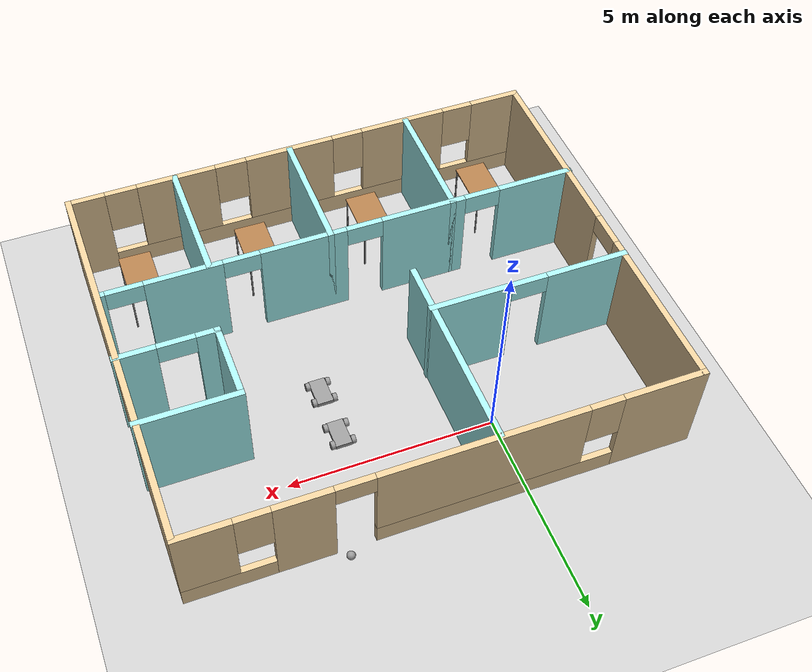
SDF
<sdf version="1.6">
 <world name="default">
  <plugin name="welcome_message" filename="libwelcome_message.so"/>
  <light name="sun" type="directional">
   <pose>0 0 10 0 -0 0</pose>
   <diffuse>0.8 0.8 0.8 1</diffuse>
   <specular>0.1 0.1 0.1 1</specular>
   <attenuation>
    <range>1000</range>
    <constant>0.9</constant>
    <linear>0.01</linear>
    <quadratic>0.001</quadratic>
   </attenuation>
   <direction>-0.5 0.5 -1</direction>
  </light>
  <model name="ground_plane">
   <static>1</static>
   <link name="link">
    <collision name="collision">
     <geometry><plane><normal>0 0 1</normal><size>100 100</size></plane></geometry>
     <surface><friction><ode><mu>100</mu><mu2>50</mu2></ode></friction></surface>
    </collision>
    <visual name="visual">
     <cast_shadows>0</cast_shadows>
     <geometry><plane><normal>0 0 1</normal><size>100 100</size></plane></geometry>
     <material>
      <script><uri>file://media/materials/scripts/gazebo.material</uri><name>Gazebo/Grey</name></script>
     </material>
    </visual>
   </link>
  </model>
  <gravity>0 0 -9.8</gravity>
  <magnetic_field>6e-06 2.3e-05 -4.2e-05</magnetic_field>
  <atmosphere type="adiabatic"/>
  <physics name="default_physics" default="0" type="ode">
   <max_step_size>0.001</max_step_size>
   <real_time_factor>1</real_time_factor>
   <real_time_update_rate>1000</real_time_update_rate>
  </physics>
  <scene><ambient>0.4 0.4 0.4 1</ambient><background>0.7 0.7 0.7 1</background><shadows>1</shadows></scene>
  <spherical_coordinates>
   <surface_model>EARTH_WGS84</surface_model>
   <latitude_deg>0</latitude_deg>
   <longitude_deg>0</longitude_deg>
   <elevation>0</elevation>
   <heading_deg>0</heading_deg>
  </spherical_coordinates>
  <model name="Building">
   <pose>1.95818 -3.03083 0 0 -0 0</pose>
   <link name="Wall_0">
    <pose>-0.006844 4.925 0 0 -0 0</pose>
    <visual name="Wall_0_Visual_0">
     <pose>-4.99079 0 1.25 0 -0 0</pose>
     <geometry><box><size>2.01841 0.15 2.5</size></box></geometry>
     <material>
      <script><uri>file://media/materials/scripts/gazebo.material</uri><name>Gazebo/Grey</name></script>
      <ambient>0.921569 0.807843 0.615686 1</ambient>
     </material>
     <meta><layer>0</layer></meta>
    </visual>
    <collision name="Wall_0_Collision_0">
     <geometry><box><size>2.01841 0.15 2.5</size></box></geometry>
     <pose>-4.99079 0 1.25 0 -0 0</pose>
    </collision>
    <visual name="Wall_0_Visual_1">
     <pose>3.22647 0 1.25 0 -0 0</pose>
     <geometry><box><size>1.33122 0.15 2.5</size></box></geometry>
     <material>
      <script><uri>file://media/materials/scripts/gazebo.material</uri><name>Gazebo/Grey</name></script>
      <ambient>0.921569 0.807843 0.615686 1</ambient>
     </material>
     <meta><layer>0</layer></meta>
    </visual>
    <collision name="Wall_0_Collision_1">
     <geometry><box><size>1.33122 0.15 2.5</size></box></geometry>
     <pose>3.22647 0 1.25 0 -0 0</pose>
    </collision>
    <visual name="Wall_0_Visual_2">
     <pose>-1.16037 0 0.25 0 -0 0</pose>
     <geometry><box><size>5.64244 0.15 0.5</size></box></geometry>
     <material>
      <script><uri>file://media/materials/scripts/gazebo.material</uri><name>Gazebo/Grey</name></script>
      <ambient>0.921569 0.807843 0.615686 1</ambient>
     </material>
     <meta><layer>0</layer></meta>
    </visual>
    <collision name="Wall_0_Collision_2">
     <geometry><box><size>5.64244 0.15 0.5</size></box></geometry>
     <pose>-1.16037 0 0.25 0 -0 0</pose>
    </collision>
    <visual name="Wall_0_Visual_3">
     <pose>4.94604 0 0.25 0 -0 0</pose>
     <geometry><box><size>2.10793 0.15 0.5</size></box></geometry>
     <material>
      <script><uri>file://media/materials/scripts/gazebo.material</uri><name>Gazebo/Grey</name></script>
      <ambient>0.921569 0.807843 0.615686 1</ambient>
     </material>
     <meta><layer>0</layer></meta>
    </visual>
    <collision name="Wall_0_Collision_3">
     <geometry><box><size>2.10793 0.15 0.5</size></box></geometry>
     <pose>4.94604 0 0.25 0 -0 0</pose>
    </collision>
    <visual name="Wall_0_Visual_4">
     <pose>-0.760365 0 1.5 0 -0 0</pose>
     <geometry><box><size>4.84244 0.15 2</size></box></geometry>
     <material>
      <script><uri>file://media/materials/scripts/gazebo.material</uri><name>Gazebo/Grey</name></script>
      <ambient>0.921569 0.807843 0.615686 1</ambient>
     </material>
     <meta><layer>0</layer></meta>
    </visual>
    <collision name="Wall_0_Collision_4">
     <geometry><box><size>4.84244 0.15 2</size></box></geometry>
     <pose>-0.760365 0 1.5 0 -0 0</pose>
    </collision>
    <visual name="Wall_0_Visual_5">
     <pose>-0.760365 0 1.5 0 -0 0</pose>
     <geometry><box><size>4.84244 0.15 2</size></box></geometry>
     <material>
      <script><uri>file://media/materials/scripts/gazebo.material</uri><name>Gazebo/Grey</name></script>
      <ambient>0.921569 0.807843 0.615686 1</ambient>
     </material>
     <meta><layer>0</layer></meta>
    </visual>
    <collision name="Wall_0_Collision_5">
     <geometry><box><size>4.84244 0.15 2</size></box></geometry>
     <pose>-0.760365 0 1.5 0 -0 0</pose>
    </collision>
    <visual name="Wall_0_Visual_6">
     <pose>5.34604 0 1.5 0 -0 0</pose>
     <geometry><box><size>1.30793 0.15 2</size></box></geometry>
     <material>
      <script><uri>file://media/materials/scripts/gazebo.material</uri><name>Gazebo/Grey</name></script>
      <ambient>0.921569 0.807843 0.615686 1</ambient>
     </material>
     <meta><layer>0</layer></meta>
    </visual>
    <collision name="Wall_0_Collision_6">
     <geometry><box><size>1.30793 0.15 2</size></box></geometry>
     <pose>5.34604 0 1.5 0 -0 0</pose>
    </collision>
    <visual name="Wall_0_Visual_7">
     <pose>-3.58159 0 1.9 0 -0 0</pose>
     <geometry><box><size>0.8 0.15 1.2</size></box></geometry>
     <material>
      <script><uri>file://media/materials/scripts/gazebo.material</uri><name>Gazebo/Grey</name></script>
      <ambient>0.921569 0.807843 0.615686 1</ambient>
     </material>
     <meta><layer>0</layer></meta>
    </visual>
    <collision name="Wall_0_Collision_7">
     <geometry><box><size>0.8 0.15 1.2</size></box></geometry>
     <pose>-3.58159 0 1.9 0 -0 0</pose>
    </collision>
    <visual name="Wall_0_Visual_8">
     <pose>4.29207 0 1.9 0 -0 0</pose>
     <geometry><box><size>0.8 0.15 1.2</size></box></geometry>
     <material>
      <script><uri>file://media/materials/scripts/gazebo.material</uri><name>Gazebo/Grey</name></script>
      <ambient>0.921569 0.807843 0.615686 1</ambient>
     </material>
     <meta><layer>0</layer></meta>
    </visual>
    <collision name="Wall_0_Collision_8">
     <geometry><box><size>0.8 0.15 1.2</size></box></geometry>
     <pose>4.29207 0 1.9 0 -0 0</pose>
    </collision>
    <visual name="Wall_0_Visual_9">
     <pose>2.11086 0 2.25 0 -0 0</pose>
     <geometry><box><size>0.9 0.15 0.5</size></box></geometry>
     <material>
      <script><uri>file://media/materials/scripts/gazebo.material</uri><name>Gazebo/Grey</name></script>
      <ambient>0.921569 0.807843 0.615686 1</ambient>
     </material>
     <meta><layer>0</layer></meta>
    </visual>
    <collision name="Wall_0_Collision_9">
     <geometry><box><size>0.9 0.15 0.5</size></box></geometry>
     <pose>2.11086 0 2.25 0 -0 0</pose>
    </collision>
    <visual name="Wall_0_Visual_10">
     <pose>2.11086 0 2.25 0 -0 0</pose>
     <geometry><box><size>0.9 0.15 0.5</size></box></geometry>
     <material>
      <script><uri>file://media/materials/scripts/gazebo.material</uri><name>Gazebo/Grey</name></script>
      <ambient>0.921569 0.807843 0.615686 1</ambient>
     </material>
     <meta><layer>0</layer></meta>
    </visual>
    <collision name="Wall_0_Collision_10">
     <geometry><box><size>0.9 0.15 0.5</size></box></geometry>
     <pose>2.11086 0 2.25 0 -0 0</pose>
    </collision>
   </link>
   <link name="Wall_1">
    <collision name="Wall_1_Collision">
     <geometry><box><size>10 0.15 2.5</size></box></geometry>
     <pose>0 0 1.25 0 -0 0</pose>
    </collision>
    <visual name="Wall_1_Visual">
     <pose>0 0 1.25 0 -0 0</pose>
     <geometry><box><size>10 0.15 2.5</size></box></geometry>
     <material>
      <script><uri>file://media/materials/scripts/gazebo.material</uri><name>Gazebo/Grey</name></script>
      <ambient>0.921569 0.807843 0.615686 1</ambient>
     </material>
     <meta><layer>0</layer></meta>
    </visual>
    <pose>5.91816 0 0 0 0 -1.5708</pose>
   </link>
   <link name="Wall_10">
    <pose>-0.033445 -1.77825 0 0 -0 0</pose>
    <visual name="Wall_10_Visual_0">
     <pose>-5.01927 0 1.25 0 -0 0</pose>
     <geometry><box><size>1.96147 0.15 2.5</size></box></geometry>
     <material>
      <script><uri>file://media/materials/scripts/gazebo.material</uri><name>Gazebo/Grey</name></script>
      <ambient>0.666667 1 1 1</ambient>
     </material>
     <meta><layer>0</layer></meta>
    </visual>
    <collision name="Wall_10_Collision_0">
     <geometry><box><size>1.96147 0.15 2.5</size></box></geometry>
     <pose>-5.01927 0 1.25 0 -0 0</pose>
    </collision>
    <visual name="Wall_10_Visual_1">
     <pose>-2.0599 0 1.25 0 -0 0</pose>
     <geometry><box><size>2.15726 0.15 2.5</size></box></geometry>
     <material>
      <script><uri>file://media/materials/scripts/gazebo.material</uri><name>Gazebo/Grey</name></script>
      <ambient>0.666667 1 1 1</ambient>
     </material>
     <meta><layer>0</layer></meta>
    </visual>
    <collision name="Wall_10_Collision_1">
     <geometry><box><size>2.15726 0.15 2.5</size></box></geometry>
     <pose>-2.0599 0 1.25 0 -0 0</pose>
    </collision>
    <visual name="Wall_10_Visual_2">
     <pose>0.99736 0 1.25 0 -0 0</pose>
     <geometry><box><size>2.15726 0.15 2.5</size></box></geometry>
     <material>
      <script><uri>file://media/materials/scripts/gazebo.material</uri><name>Gazebo/Grey</name></script>
      <ambient>0.666667 1 1 1</ambient>
     </material>
     <meta><layer>0</layer></meta>
    </visual>
    <collision name="Wall_10_Collision_2">
     <geometry><box><size>2.15726 0.15 2.5</size></box></geometry>
     <pose>0.99736 0 1.25 0 -0 0</pose>
    </collision>
    <visual name="Wall_10_Visual_3">
     <pose>3.92388 0 1.25 0 -0 0</pose>
     <geometry><box><size>1.89579 0.15 2.5</size></box></geometry>
     <material>
      <script><uri>file://media/materials/scripts/gazebo.material</uri><name>Gazebo/Grey</name></script>
      <ambient>0.666667 1 1 1</ambient>
     </material>
     <meta><layer>0</layer></meta>
    </visual>
    <collision name="Wall_10_Collision_3">
     <geometry><box><size>1.89579 0.15 2.5</size></box></geometry>
     <pose>3.92388 0 1.25 0 -0 0</pose>
    </collision>
    <visual name="Wall_10_Visual_4">
     <pose>5.88589 0 1.25 0 -0 0</pose>
     <geometry><box><size>0.228222 0.15 2.5</size></box></geometry>
     <material>
      <script><uri>file://media/materials/scripts/gazebo.material</uri><name>Gazebo/Grey</name></script>
      <ambient>0.666667 1 1 1</ambient>
     </material>
     <meta><layer>0</layer></meta>
    </visual>
    <collision name="Wall_10_Collision_4">
     <geometry><box><size>0.228222 0.15 2.5</size></box></geometry>
     <pose>5.88589 0 1.25 0 -0 0</pose>
    </collision>
    <visual name="Wall_10_Visual_5">
     <pose>-3.58853 0 2.25 0 -0 0</pose>
     <geometry><box><size>0.9 0.15 0.5</size></box></geometry>
     <material>
      <script><uri>file://media/materials/scripts/gazebo.material</uri><name>Gazebo/Grey</name></script>
      <ambient>0.666667 1 1 1</ambient>
     </material>
     <meta><layer>0</layer></meta>
    </visual>
    <collision name="Wall_10_Collision_5">
     <geometry><box><size>0.9 0.15 0.5</size></box></geometry>
     <pose>-3.58853 0 2.25 0 -0 0</pose>
    </collision>
    <visual name="Wall_10_Visual_6">
     <pose>-0.531272 0 2.25 0 -0 0</pose>
     <geometry><box><size>0.9 0.15 0.5</size></box></geometry>
     <material>
      <script><uri>file://media/materials/scripts/gazebo.material</uri><name>Gazebo/Grey</name></script>
      <ambient>0.666667 1 1 1</ambient>
     </material>
     <meta><layer>0</layer></meta>
    </visual>
    <collision name="Wall_10_Collision_6">
     <geometry><box><size>0.9 0.15 0.5</size></box></geometry>
     <pose>-0.531272 0 2.25 0 -0 0</pose>
    </collision>
    <visual name="Wall_10_Visual_7">
     <pose>2.52599 0 2.25 0 -0 0</pose>
     <geometry><box><size>0.9 0.15 0.5</size></box></geometry>
     <material>
      <script><uri>file://media/materials/scripts/gazebo.material</uri><name>Gazebo/Grey</name></script>
      <ambient>0.666667 1 1 1</ambient>
     </material>
     <meta><layer>0</layer></meta>
    </visual>
    <collision name="Wall_10_Collision_7">
     <geometry><box><size>0.9 0.15 0.5</size></box></geometry>
     <pose>2.52599 0 2.25 0 -0 0</pose>
    </collision>
    <visual name="Wall_10_Visual_8">
     <pose>5.32178 0 2.25 0 -0 0</pose>
     <geometry><box><size>0.9 0.15 0.5</size></box></geometry>
     <material>
      <script><uri>file://media/materials/scripts/gazebo.material</uri><name>Gazebo/Grey</name></script>
      <ambient>0.666667 1 1 1</ambient>
     </material>
     <meta><layer>0</layer></meta>
    </visual>
    <collision name="Wall_10_Collision_8">
     <geometry><box><size>0.9 0.15 0.5</size></box></geometry>
     <pose>5.32178 0 2.25 0 -0 0</pose>
    </collision>
   </link>
   <link name="Wall_12">
    <collision name="Wall_12_Collision">
     <geometry><box><size>3.25 0.15 2.5</size></box></geometry>
     <pose>0 0 1.25 0 -0 0</pose>
    </collision>
    <visual name="Wall_12_Visual">
     <pose>0 0 1.25 0 -0 0</pose>
     <geometry><box><size>3.25 0.15 2.5</size></box></geometry>
     <material>
      <script><uri>file://media/materials/scripts/gazebo.material</uri><name>Gazebo/Grey</name></script>
      <ambient>0.666667 1 1 1</ambient>
     </material>
     <meta><layer>0</layer></meta>
    </visual>
    <pose>-2.84622 -3.32825 0 0 0 -1.5708</pose>
   </link>
   <link name="Wall_14">
    <collision name="Wall_14_Collision">
     <geometry><box><size>3.25 0.15 2.5</size></box></geometry>
     <pose>0 0 1.25 0 -0 0</pose>
    </collision>
    <visual name="Wall_14_Visual">
     <pose>0 0 1.25 0 -0 0</pose>
     <geometry><box><size>3.25 0.15 2.5</size></box></geometry>
     <material>
      <script><uri>file://media/materials/scripts/gazebo.material</uri><name>Gazebo/Grey</name></script>
      <ambient>0.666667 1 1 1</ambient>
     </material>
     <meta><layer>0</layer></meta>
    </visual>
    <pose>0.292602 -3.32825 0 0 0 -1.5708</pose>
   </link>
   <link name="Wall_16">
    <collision name="Wall_16_Collision">
     <geometry><box><size>3.25 0.15 2.5</size></box></geometry>
     <pose>0 0 1.25 0 -0 0</pose>
    </collision>
    <visual name="Wall_16_Visual">
     <pose>0 0 1.25 0 -0 0</pose>
     <geometry><box><size>3.25 0.15 2.5</size></box></geometry>
     <material>
      <script><uri>file://media/materials/scripts/gazebo.material</uri><name>Gazebo/Grey</name></script>
      <ambient>0.666667 1 1 1</ambient>
     </material>
     <meta><layer>0</layer></meta>
    </visual>
    <pose>3.27182 -3.35485 0 0 0 -1.5708</pose>
   </link>
   <link name="Wall_18">
    <collision name="Wall_18_Collision">
     <geometry><box><size>5 0.15 2.5</size></box></geometry>
     <pose>0 0 1.25 0 -0 0</pose>
    </collision>
    <visual name="Wall_18_Visual">
     <pose>0 0 1.25 0 -0 0</pose>
     <geometry><box><size>5 0.15 2.5</size></box></geometry>
     <material>
      <script><uri>file://media/materials/scripts/gazebo.material</uri><name>Gazebo/Grey</name></script>
      <ambient>0.666667 1 1 1</ambient>
     </material>
     <meta><layer>0</layer></meta>
    </visual>
    <pose>-1.11721 2.45556 0 0 -0 1.5708</pose>
   </link>
   <link name="Wall_2">
    <pose>-0.006844 -4.925 0 0 -0 3.14159</pose>
    <visual name="Wall_2_Visual_0">
     <pose>-5.51894 0 1.25 0 -0 0</pose>
     <geometry><box><size>0.962125 0.15 2.5</size></box></geometry>
     <material>
      <script><uri>file://media/materials/scripts/gazebo.material</uri><name>Gazebo/Grey</name></script>
      <ambient>0.921569 0.807843 0.615686 1</ambient>
     </material>
     <meta><layer>0</layer></meta>
    </visual>
    <collision name="Wall_2_Collision_0">
     <geometry><box><size>0.962125 0.15 2.5</size></box></geometry>
     <pose>-5.51894 0 1.25 0 -0 0</pose>
    </collision>
    <visual name="Wall_2_Visual_1">
     <pose>0.481062 0 0.25 0 -0 0</pose>
     <geometry><box><size>11.0379 0.15 0.5</size></box></geometry>
     <material>
      <script><uri>file://media/materials/scripts/gazebo.material</uri><name>Gazebo/Grey</name></script>
      <ambient>0.921569 0.807843 0.615686 1</ambient>
     </material>
     <meta><layer>0</layer></meta>
    </visual>
    <collision name="Wall_2_Collision_1">
     <geometry><box><size>11.0379 0.15 0.5</size></box></geometry>
     <pose>0.481062 0 0.25 0 -0 0</pose>
    </collision>
    <visual name="Wall_2_Visual_2">
     <pose>-3.24137 0 1.5 0 -0 0</pose>
     <geometry><box><size>1.99302 0.15 2</size></box></geometry>
     <material>
      <script><uri>file://media/materials/scripts/gazebo.material</uri><name>Gazebo/Grey</name></script>
      <ambient>0.921569 0.807843 0.615686 1</ambient>
     </material>
     <meta><layer>0</layer></meta>
    </visual>
    <collision name="Wall_2_Collision_2">
     <geometry><box><size>1.99302 0.15 2</size></box></geometry>
     <pose>-3.24137 0 1.5 0 -0 0</pose>
    </collision>
    <visual name="Wall_2_Visual_3">
     <pose>-0.302043 0 1.5 0 -0 0</pose>
     <geometry><box><size>2.28562 0.15 2</size></box></geometry>
     <material>
      <script><uri>file://media/materials/scripts/gazebo.material</uri><name>Gazebo/Grey</name></script>
      <ambient>0.921569 0.807843 0.615686 1</ambient>
     </material>
     <meta><layer>0</layer></meta>
    </visual>
    <collision name="Wall_2_Collision_3">
     <geometry><box><size>2.28562 0.15 2</size></box></geometry>
     <pose>-0.302043 0 1.5 0 -0 0</pose>
    </collision>
    <visual name="Wall_2_Visual_4">
     <pose>2.75698 0 1.5 0 -0 0</pose>
     <geometry><box><size>2.23242 0.15 2</size></box></geometry>
     <material>
      <script><uri>file://media/materials/scripts/gazebo.material</uri><name>Gazebo/Grey</name></script>
      <ambient>0.921569 0.807843 0.615686 1</ambient>
     </material>
     <meta><layer>0</layer></meta>
    </visual>
    <collision name="Wall_2_Collision_4">
     <geometry><box><size>2.23242 0.15 2</size></box></geometry>
     <pose>2.75698 0 1.5 0 -0 0</pose>
    </collision>
    <visual name="Wall_2_Visual_5">
     <pose>5.3366 0 1.5 0 -0 0</pose>
     <geometry><box><size>1.32681 0.15 2</size></box></geometry>
     <material>
      <script><uri>file://media/materials/scripts/gazebo.material</uri><name>Gazebo/Grey</name></script>
      <ambient>0.921569 0.807843 0.615686 1</ambient>
     </material>
     <meta><layer>0</layer></meta>
    </visual>
    <collision name="Wall_2_Collision_5">
     <geometry><box><size>1.32681 0.15 2</size></box></geometry>
     <pose>5.3366 0 1.5 0 -0 0</pose>
    </collision>
    <visual name="Wall_2_Visual_6">
     <pose>-4.63788 0 1.9 0 -0 0</pose>
     <geometry><box><size>0.8 0.15 1.2</size></box></geometry>
     <material>
      <script><uri>file://media/materials/scripts/gazebo.material</uri><name>Gazebo/Grey</name></script>
      <ambient>0.921569 0.807843 0.615686 1</ambient>
     </material>
     <meta><layer>0</layer></meta>
    </visual>
    <collision name="Wall_2_Collision_6">
     <geometry><box><size>0.8 0.15 1.2</size></box></geometry>
     <pose>-4.63788 0 1.9 0 -0 0</pose>
    </collision>
    <visual name="Wall_2_Visual_7">
     <pose>-1.84485 0 1.9 0 -0 0</pose>
     <geometry><box><size>0.8 0.15 1.2</size></box></geometry>
     <material>
      <script><uri>file://media/materials/scripts/gazebo.material</uri><name>Gazebo/Grey</name></script>
      <ambient>0.921569 0.807843 0.615686 1</ambient>
     </material>
     <meta><layer>0</layer></meta>
    </visual>
    <collision name="Wall_2_Collision_7">
     <geometry><box><size>0.8 0.15 1.2</size></box></geometry>
     <pose>-1.84485 0 1.9 0 -0 0</pose>
    </collision>
    <visual name="Wall_2_Visual_8">
     <pose>1.24077 0 1.9 0 -0 0</pose>
     <geometry><box><size>0.8 0.15 1.2</size></box></geometry>
     <material>
      <script><uri>file://media/materials/scripts/gazebo.material</uri><name>Gazebo/Grey</name></script>
      <ambient>0.921569 0.807843 0.615686 1</ambient>
     </material>
     <meta><layer>0</layer></meta>
    </visual>
    <collision name="Wall_2_Collision_8">
     <geometry><box><size>0.8 0.15 1.2</size></box></geometry>
     <pose>1.24077 0 1.9 0 -0 0</pose>
    </collision>
    <visual name="Wall_2_Visual_9">
     <pose>4.27319 0 1.9 0 -0 0</pose>
     <geometry><box><size>0.8 0.15 1.2</size></box></geometry>
     <material>
      <script><uri>file://media/materials/scripts/gazebo.material</uri><name>Gazebo/Grey</name></script>
      <ambient>0.921569 0.807843 0.615686 1</ambient>
     </material>
     <meta><layer>0</layer></meta>
    </visual>
    <collision name="Wall_2_Collision_9">
     <geometry><box><size>0.8 0.15 1.2</size></box></geometry>
     <pose>4.27319 0 1.9 0 -0 0</pose>
    </collision>
   </link>
   <link name="Wall_20">
    <pose>-3.51561 1.20097 0 0 -0 3.14159</pose>
    <visual name="Wall_20_Visual_0">
     <pose>-1.48215 0 1.25 0 -0 0</pose>
     <geometry><box><size>2.03569 0.15 2.5</size></box></geometry>
     <material>
      <script><uri>file://media/materials/scripts/gazebo.material</uri><name>Gazebo/Grey</name></script>
      <ambient>0.666667 1 1 1</ambient>
     </material>
     <meta><layer>0</layer></meta>
    </visual>
    <collision name="Wall_20_Collision_0">
     <geometry><box><size>2.03569 0.15 2.5</size></box></geometry>
     <pose>-1.48215 0 1.25 0 -0 0</pose>
    </collision>
    <visual name="Wall_20_Visual_1">
     <pose>1.46785 0 1.25 0 -0 0</pose>
     <geometry><box><size>2.06431 0.15 2.5</size></box></geometry>
     <material>
      <script><uri>file://media/materials/scripts/gazebo.material</uri><name>Gazebo/Grey</name></script>
      <ambient>0.666667 1 1 1</ambient>
     </material>
     <meta><layer>0</layer></meta>
    </visual>
    <collision name="Wall_20_Collision_1">
     <geometry><box><size>2.06431 0.15 2.5</size></box></geometry>
     <pose>1.46785 0 1.25 0 -0 0</pose>
    </collision>
    <visual name="Wall_20_Visual_2">
     <pose>-0.01431 0 2.25 0 -0 0</pose>
     <geometry><box><size>0.9 0.15 0.5</size></box></geometry>
     <material>
      <script><uri>file://media/materials/scripts/gazebo.material</uri><name>Gazebo/Grey</name></script>
      <ambient>0.666667 1 1 1</ambient>
     </material>
     <meta><layer>0</layer></meta>
    </visual>
    <collision name="Wall_20_Collision_2">
     <geometry><box><size>0.9 0.15 0.5</size></box></geometry>
     <pose>-0.01431 0 2.25 0 -0 0</pose>
    </collision>
   </link>
   <link name="Wall_3">
    <pose>-5.93184 0 0 0 -0 1.5708</pose>
    <visual name="Wall_3_Visual_0">
     <pose>-2.53881 0 1.25 0 -0 0</pose>
     <geometry><box><size>4.92239 0.15 2.5</size></box></geometry>
     <material>
      <script><uri>file://media/materials/scripts/gazebo.material</uri><name>Gazebo/Grey</name></script>
      <ambient>0.921569 0.807843 0.615686 1</ambient>
     </material>
     <meta><layer>0</layer></meta>
    </visual>
    <collision name="Wall_3_Collision_0">
     <geometry><box><size>4.92239 0.15 2.5</size></box></geometry>
     <pose>-2.53881 0 1.25 0 -0 0</pose>
    </collision>
    <visual name="Wall_3_Visual_1">
     <pose>2.91119 0 1.25 0 -0 0</pose>
     <geometry><box><size>4.17762 0.15 2.5</size></box></geometry>
     <material>
      <script><uri>file://media/materials/scripts/gazebo.material</uri><name>Gazebo/Grey</name></script>
      <ambient>0.921569 0.807843 0.615686 1</ambient>
     </material>
     <meta><layer>0</layer></meta>
    </visual>
    <collision name="Wall_3_Collision_1">
     <geometry><box><size>4.17762 0.15 2.5</size></box></geometry>
     <pose>2.91119 0 1.25 0 -0 0</pose>
    </collision>
    <visual name="Wall_3_Visual_2">
     <pose>0.372385 0 2.25 0 -0 0</pose>
     <geometry><box><size>0.9 0.15 0.5</size></box></geometry>
     <material>
      <script><uri>file://media/materials/scripts/gazebo.material</uri><name>Gazebo/Grey</name></script>
      <ambient>0.921569 0.807843 0.615686 1</ambient>
     </material>
     <meta><layer>0</layer></meta>
    </visual>
    <collision name="Wall_3_Collision_2">
     <geometry><box><size>0.9 0.15 0.5</size></box></geometry>
     <pose>0.372385 0 2.25 0 -0 0</pose>
    </collision>
   </link>
   <link name="Wall_6">
    <collision name="Wall_6_Collision">
     <geometry><box><size>2.5 0.15 2.5</size></box></geometry>
     <pose>0 0 1.25 0 -0 0</pose>
    </collision>
    <visual name="Wall_6_Visual">
     <pose>0 0 1.25 0 -0 0</pose>
     <geometry><box><size>2.5 0.15 2.5</size></box></geometry>
     <material>
      <script><uri>file://media/materials/scripts/gazebo.material</uri><name>Gazebo/Grey</name></script>
      <ambient>0.666667 1 1 1</ambient>
     </material>
     <meta><layer>0</layer></meta>
    </visual>
    <pose>4.78344 1.97238 0 0 -0 3.14159</pose>
   </link>
   <link name="Wall_7">
    <collision name="Wall_7_Collision">
     <geometry><box><size>2 0.15 2.5</size></box></geometry>
     <pose>0 0 1.25 0 -0 0</pose>
    </collision>
    <visual name="Wall_7_Visual">
     <pose>0 0 1.25 0 -0 0</pose>
     <geometry><box><size>2 0.15 2.5</size></box></geometry>
     <material>
      <script><uri>file://media/materials/scripts/gazebo.material</uri><name>Gazebo/Grey</name></script>
      <ambient>0.666667 1 1 1</ambient>
     </material>
     <meta><layer>0</layer></meta>
    </visual>
    <pose>3.60844 1.04738 0 0 0 -1.5708</pose>
   </link>
   <link name="Wall_8">
    <pose>4.78344 0.122378 0 0 -0 0</pose>
    <visual name="Wall_8_Visual_0">
     <pose>-0.9596 0 1.25 0 -0 0</pose>
     <geometry><box><size>0.5808 0.15 2.5</size></box></geometry>
     <material>
      <script><uri>file://media/materials/scripts/gazebo.material</uri><name>Gazebo/Grey</name></script>
      <ambient>0.666667 1 1 1</ambient>
     </material>
     <meta><layer>0</layer></meta>
    </visual>
    <collision name="Wall_8_Collision_0">
     <geometry><box><size>0.5808 0.15 2.5</size></box></geometry>
     <pose>-0.9596 0 1.25 0 -0 0</pose>
    </collision>
    <visual name="Wall_8_Visual_1">
     <pose>0.7404 0 1.25 0 -0 0</pose>
     <geometry><box><size>1.0192 0.15 2.5</size></box></geometry>
     <material>
      <script><uri>file://media/materials/scripts/gazebo.material</uri><name>Gazebo/Grey</name></script>
      <ambient>0.666667 1 1 1</ambient>
     </material>
     <meta><layer>0</layer></meta>
    </visual>
    <collision name="Wall_8_Collision_1">
     <geometry><box><size>1.0192 0.15 2.5</size></box></geometry>
     <pose>0.7404 0 1.25 0 -0 0</pose>
    </collision>
    <visual name="Wall_8_Visual_2">
     <pose>-0.2192 0 2.25 0 -0 0</pose>
     <geometry><box><size>0.9 0.15 0.5</size></box></geometry>
     <material>
      <script><uri>file://media/materials/scripts/gazebo.material</uri><name>Gazebo/Grey</name></script>
      <ambient>0.666667 1 1 1</ambient>
     </material>
     <meta><layer>0</layer></meta>
    </visual>
    <collision name="Wall_8_Collision_2">
     <geometry><box><size>0.9 0.15 0.5</size></box></geometry>
     <pose>-0.2192 0 2.25 0 -0 0</pose>
    </collision>
   </link>
   <static>1</static>
  </model>
  <model name="Robot">
   <link name="link_0">
    <inertial>
     <mass>1</mass>
     <inertia>
      <ixx>0.166667</ixx>
      <ixy>0</ixy>
      <ixz>0</ixz>
      <iyy>0.166667</iyy>
      <iyz>0</iyz>
      <izz>0.166667</izz>
     </inertia>
    </inertial>
    <visual name="visual">
     <geometry><box><size>0.4 0.7 0.1</size></box></geometry>
     <material>
      <lighting>1</lighting>
      <script><uri>file://media/materials/scripts/gazebo.material</uri><name>Gazebo/Grey</name></script>
      <shader type="pixel"><normal_map>__default__</normal_map></shader>
      <ambient>0.3 0.3 0.3 1</ambient>
      <diffuse>0.7 0.7 0.7 1</diffuse>
      <specular>0.01 0.01 0.01 1</specular>
      <emissive>0 0 0 1</emissive>
     </material>
    </visual>
    <collision name="collision">
     <geometry><box><size>0.4 0.7 0.1</size></box></geometry>
     <surface>
      <friction>
       <ode><mu>1</mu><mu2>1</mu2><fdir1>0 0 0</fdir1><slip1>0</slip1><slip2>0</slip2></ode>
       <torsional>
        <coefficient>1</coefficient>
        <patch_radius>0</patch_radius>
        <surface_radius>0</surface_radius>
        <use_patch_radius>1</use_patch_radius>
        <ode><slip>0</slip></ode>
       </torsional>
      </friction>
      <bounce><restitution_coefficient>0</restitution_coefficient><threshold>1e+06</threshold></bounce>
      <contact>
       <collide_without_contact>0</collide_without_contact>
       <collide_without_contact_bitmask>1</collide_without_contact_bitmask>
       <collide_bitmask>1</collide_bitmask>
       <ode>
        <soft_cfm>0</soft_cfm>
        <soft_erp>0.2</soft_erp>
        <kp>1e+13</kp>
        <kd>1</kd>
        <max_vel>0.01</max_vel>
        <min_depth>0</min_depth>
       </ode>
       <bullet>
        <split_impulse>1</split_impulse>
        <split_impulse_penetration_threshold>-0.01</split_impulse_penetration_threshold>
        <soft_cfm>0</soft_cfm>
        <soft_erp>0.2</soft_erp>
        <kp>1e+13</kp>
        <kd>1</kd>
       </bullet>
      </contact>
     </surface>
    </collision>
   </link>
   <link name="link_1">
    <pose>0.25 -0.25 0 0 -0 0</pose>
    <inertial>
     <mass>1</mass>
     <inertia><ixx>0.145833</ixx><ixy>0</ixy><ixz>0</ixz><iyy>0.145833</iyy><iyz>0</iyz><izz>0.125</izz></inertia>
    </inertial>
    <visual name="visual">
     <pose>0 0 0 3.14159 1.57079 3.14159</pose>
     <geometry><cylinder><radius>0.1</radius><length>0.1</length></cylinder></geometry>
     <material>
      <lighting>1</lighting>
      <script><uri>file://media/materials/scripts/gazebo.material</uri><name>Gazebo/Grey</name></script>
      <shader type="pixel"><normal_map>__default__</normal_map></shader>
      <ambient>0.3 0.3 0.3 1</ambient>
      <diffuse>0.7 0.7 0.7 1</diffuse>
      <specular>0.01 0.01 0.01 1</specular>
      <emissive>0 0 0 1</emissive>
     </material>
    </visual>
    <collision name="collision">
     <pose>0 0 0 3.14159 1.57079 3.14159</pose>
     <geometry><cylinder><radius>0.1</radius><length>0.1</length></cylinder></geometry>
     <surface>
      <friction>
       <ode><mu>1</mu><mu2>1</mu2><fdir1>0 0 0</fdir1><slip1>0</slip1><slip2>0</slip2></ode>
       <torsional>
        <coefficient>1</coefficient>
        <patch_radius>0</patch_radius>
        <surface_radius>0</surface_radius>
        <use_patch_radius>1</use_patch_radius>
        <ode><slip>0</slip></ode>
       </torsional>
      </friction>
      <bounce><restitution_coefficient>0</restitution_coefficient><threshold>1e+06</threshold></bounce>
      <contact>
       <collide_without_contact>0</collide_without_contact>
       <collide_without_contact_bitmask>1</collide_without_contact_bitmask>
       <collide_bitmask>1</collide_bitmask>
       <ode>
        <soft_cfm>0</soft_cfm>
        <soft_erp>0.2</soft_erp>
        <kp>1e+13</kp>
        <kd>1</kd>
        <max_vel>0.01</max_vel>
        <min_depth>0</min_depth>
       </ode>
       <bullet>
        <split_impulse>1</split_impulse>
        <split_impulse_penetration_threshold>-0.01</split_impulse_penetration_threshold>
        <soft_cfm>0</soft_cfm>
        <soft_erp>0.2</soft_erp>
        <kp>1e+13</kp>
        <kd>1</kd>
       </bullet>
      </contact>
     </surface>
    </collision>
   </link>
   <link name="link_1_clone">
    <pose>0.25 0.25 0 0 -0 0</pose>
    <inertial>
     <mass>1</mass>
     <inertia><ixx>0.145833</ixx><ixy>0</ixy><ixz>0</ixz><iyy>0.145833</iyy><iyz>0</iyz><izz>0.125</izz></inertia>
    </inertial>
    <visual name="visual">
     <pose>0 0 0 3.14159 1.57079 3.14159</pose>
     <geometry><cylinder><radius>0.1</radius><length>0.1</length></cylinder></geometry>
     <material>
      <lighting>1</lighting>
      <script><uri>file://media/materials/scripts/gazebo.material</uri><name>Gazebo/Grey</name></script>
      <shader type="pixel"><normal_map>__default__</normal_map></shader>
      <ambient>0.3 0.3 0.3 1</ambient>
      <diffuse>0.7 0.7 0.7 1</diffuse>
      <specular>0.01 0.01 0.01 1</specular>
      <emissive>0 0 0 1</emissive>
     </material>
    </visual>
    <collision name="collision">
     <pose>0 0 0 3.14159 1.57079 3.14159</pose>
     <geometry><cylinder><radius>0.1</radius><length>0.1</length></cylinder></geometry>
     <surface>
      <friction>
       <ode><mu>1</mu><mu2>1</mu2><fdir1>0 0 0</fdir1><slip1>0</slip1><slip2>0</slip2></ode>
       <torsional>
        <coefficient>1</coefficient>
        <patch_radius>0</patch_radius>
        <surface_radius>0</surface_radius>
        <use_patch_radius>1</use_patch_radius>
        <ode><slip>0</slip></ode>
       </torsional>
      </friction>
      <bounce><restitution_coefficient>0</restitution_coefficient><threshold>1e+06</threshold></bounce>
      <contact>
       <collide_without_contact>0</collide_without_contact>
       <collide_without_contact_bitmask>1</collide_without_contact_bitmask>
       <collide_bitmask>1</collide_bitmask>
       <ode>
        <soft_cfm>0</soft_cfm>
        <soft_erp>0.2</soft_erp>
        <kp>1e+13</kp>
        <kd>1</kd>
        <max_vel>0.01</max_vel>
        <min_depth>0</min_depth>
       </ode>
       <bullet>
        <split_impulse>1</split_impulse>
        <split_impulse_penetration_threshold>-0.01</split_impulse_penetration_threshold>
        <soft_cfm>0</soft_cfm>
        <soft_erp>0.2</soft_erp>
        <kp>1e+13</kp>
        <kd>1</kd>
       </bullet>
      </contact>
     </surface>
    </collision>
   </link>
   <link name="link_1_clone_0">
    <pose>-0.250001 -0.25 0 0 -0 0</pose>
    <inertial>
     <mass>1</mass>
     <inertia><ixx>0.145833</ixx><ixy>0</ixy><ixz>0</ixz><iyy>0.145833</iyy><iyz>0</iyz><izz>0.125</izz></inertia>
    </inertial>
    <visual name="visual">
     <pose>0 0 0 3.14159 1.57079 3.14159</pose>
     <geometry><cylinder><radius>0.1</radius><length>0.1</length></cylinder></geometry>
     <material>
      <lighting>1</lighting>
      <script><uri>file://media/materials/scripts/gazebo.material</uri><name>Gazebo/Grey</name></script>
      <shader type="pixel"><normal_map>__default__</normal_map></shader>
      <ambient>0.3 0.3 0.3 1</ambient>
      <diffuse>0.7 0.7 0.7 1</diffuse>
      <specular>0.01 0.01 0.01 1</specular>
      <emissive>0 0 0 1</emissive>
     </material>
    </visual>
    <collision name="collision">
     <pose>0 0 0 3.14159 1.57079 3.14159</pose>
     <geometry><cylinder><radius>0.1</radius><length>0.1</length></cylinder></geometry>
     <surface>
      <friction>
       <ode><mu>1</mu><mu2>1</mu2><fdir1>0 0 0</fdir1><slip1>0</slip1><slip2>0</slip2></ode>
       <torsional>
        <coefficient>1</coefficient>
        <patch_radius>0</patch_radius>
        <surface_radius>0</surface_radius>
        <use_patch_radius>1</use_patch_radius>
        <ode><slip>0</slip></ode>
       </torsional>
      </friction>
      <bounce><restitution_coefficient>0</restitution_coefficient><threshold>1e+06</threshold></bounce>
      <contact>
       <collide_without_contact>0</collide_without_contact>
       <collide_without_contact_bitmask>1</collide_without_contact_bitmask>
       <collide_bitmask>1</collide_bitmask>
       <ode>
        <soft_cfm>0</soft_cfm>
        <soft_erp>0.2</soft_erp>
        <kp>1e+13</kp>
        <kd>1</kd>
        <max_vel>0.01</max_vel>
        <min_depth>0</min_depth>
       </ode>
       <bullet>
        <split_impulse>1</split_impulse>
        <split_impulse_penetration_threshold>-0.01</split_impulse_penetration_threshold>
        <soft_cfm>0</soft_cfm>
        <soft_erp>0.2</soft_erp>
        <kp>1e+13</kp>
        <kd>1</kd>
       </bullet>
      </contact>
     </surface>
    </collision>
   </link>
   <link name="link_1_clone_1">
    <pose>-0.250001 0.25 0 0 -0 0</pose>
    <inertial>
     <mass>1</mass>
     <inertia><ixx>0.145833</ixx><ixy>0</ixy><ixz>0</ixz><iyy>0.145833</iyy><iyz>0</iyz><izz>0.125</izz></inertia>
    </inertial>
    <visual name="visual">
     <pose>0 0 0 3.14159 1.57079 3.14159</pose>
     <geometry><cylinder><radius>0.1</radius><length>0.1</length></cylinder></geometry>
     <material>
      <lighting>1</lighting>
      <script><uri>file://media/materials/scripts/gazebo.material</uri><name>Gazebo/Grey</name></script>
      <shader type="pixel"><normal_map>__default__</normal_map></shader>
      <ambient>0.3 0.3 0.3 1</ambient>
      <diffuse>0.7 0.7 0.7 1</diffuse>
      <specular>0.01 0.01 0.01 1</specular>
      <emissive>0 0 0 1</emissive>
     </material>
    </visual>
    <collision name="collision">
     <pose>0 0 0 3.14159 1.57079 3.14159</pose>
     <geometry><cylinder><radius>0.1</radius><length>0.1</length></cylinder></geometry>
     <surface>
      <friction>
       <ode><mu>1</mu><mu2>1</mu2><fdir1>0 0 0</fdir1><slip1>0</slip1><slip2>0</slip2></ode>
       <torsional>
        <coefficient>1</coefficient>
        <patch_radius>0</patch_radius>
        <surface_radius>0</surface_radius>
        <use_patch_radius>1</use_patch_radius>
        <ode><slip>0</slip></ode>
       </torsional>
      </friction>
      <bounce><restitution_coefficient>0</restitution_coefficient><threshold>1e+06</threshold></bounce>
      <contact>
       <collide_without_contact>0</collide_without_contact>
       <collide_without_contact_bitmask>1</collide_without_contact_bitmask>
       <collide_bitmask>1</collide_bitmask>
       <ode>
        <soft_cfm>0</soft_cfm>
        <soft_erp>0.2</soft_erp>
        <kp>1e+13</kp>
        <kd>1</kd>
        <max_vel>0.01</max_vel>
        <min_depth>0</min_depth>
       </ode>
       <bullet>
        <split_impulse>1</split_impulse>
        <split_impulse_penetration_threshold>-0.01</split_impulse_penetration_threshold>
        <soft_cfm>0</soft_cfm>
        <soft_erp>0.2</soft_erp>
        <kp>1e+13</kp>
        <kd>1</kd>
       </bullet>
      </contact>
     </surface>
    </collision>
   </link>
   <joint name="link_0_JOINT_0" type="revolute">
    <parent>link_0</parent>
    <child>link_1_clone</child>
    <axis>
     <xyz>1 0 0</xyz>
     <use_parent_model_frame>0</use_parent_model_frame>
     <limit>
      <lower>-1.79769e+308</lower>
      <upper>1.79769e+308</upper>
      <effort>-1</effort>
      <velocity>-1</velocity>
     </limit>
     <dynamics>
      <spring_reference>0</spring_reference>
      <spring_stiffness>0</spring_stiffness>
      <damping>0</damping>
     </dynamics>
    </axis>
    <physics>
     <ode><limit><cfm>0</cfm><erp>0.2</erp></limit><suspension><cfm>0</cfm><erp>0.2</erp></suspension></ode>
    </physics>
   </joint>
   <joint name="link_0_JOINT_1" type="revolute">
    <parent>link_0</parent>
    <child>link_1_clone_1</child>
    <axis>
     <xyz>1 0 0</xyz>
     <use_parent_model_frame>0</use_parent_model_frame>
     <limit>
      <lower>-1.79769e+308</lower>
      <upper>1.79769e+308</upper>
      <effort>-1</effort>
      <velocity>-1</velocity>
     </limit>
     <dynamics>
      <spring_reference>0</spring_reference>
      <spring_stiffness>0</spring_stiffness>
      <damping>0</damping>
     </dynamics>
    </axis>
    <physics>
     <ode><limit><cfm>0</cfm><erp>0.2</erp></limit><suspension><cfm>0</cfm><erp>0.2</erp></suspension></ode>
    </physics>
   </joint>
   <joint name="link_0_JOINT_2" type="revolute">
    <parent>link_0</parent>
    <child>link_1</child>
    <axis>
     <xyz>1 0 0</xyz>
     <use_parent_model_frame>0</use_parent_model_frame>
     <limit>
      <lower>-1.79769e+308</lower>
      <upper>1.79769e+308</upper>
      <effort>-1</effort>
      <velocity>-1</velocity>
     </limit>
     <dynamics>
      <spring_reference>0</spring_reference>
      <spring_stiffness>0</spring_stiffness>
      <damping>0</damping>
     </dynamics>
    </axis>
    <physics>
     <ode><limit><cfm>0</cfm><erp>0.2</erp></limit><suspension><cfm>0</cfm><erp>0.2</erp></suspension></ode>
    </physics>
   </joint>
   <joint name="link_0_JOINT_3" type="revolute">
    <parent>link_0</parent>
    <child>link_1_clone_0</child>
    <axis>
     <xyz>1 0 0</xyz>
     <use_parent_model_frame>0</use_parent_model_frame>
     <limit>
      <lower>-1.79769e+308</lower>
      <upper>1.79769e+308</upper>
      <effort>-1</effort>
      <velocity>-1</velocity>
     </limit>
     <dynamics>
      <spring_reference>0</spring_reference>
      <spring_stiffness>0</spring_stiffness>
      <damping>0</damping>
     </dynamics>
    </axis>
    <physics>
     <ode><limit><cfm>0</cfm><erp>0.2</erp></limit><suspension><cfm>0</cfm><erp>0.2</erp></suspension></ode>
    </physics>
   </joint>
   <static>0</static>
   <pose>3.47069 -2.16442 0.099998 1e-05 -0 0.004193</pose>
  </model>
  <model name="table">
   <static>1</static>
   <link name="link">
    <collision name="surface">
     <pose>0 0 1 0 -0 0</pose>
     <geometry><box><size>1.5 0.8 0.03</size></box></geometry>
     <surface><friction><ode><mu>0.6</mu><mu2>0.6</mu2></ode></friction></surface>
    </collision>
    <visual name="visual1">
     <pose>0 0 1 0 -0 0</pose>
     <geometry><box><size>1.5 0.8 0.03</size></box></geometry>
     <material>
      <script><uri>file://media/materials/scripts/gazebo.material</uri><name>Gazebo/Wood</name></script>
     </material>
    </visual>
    <collision name="front_left_leg">
     <pose>0.68 0.38 0.5 0 -0 0</pose>
     <geometry><cylinder><radius>0.02</radius><length>1</length></cylinder></geometry>
    </collision>
    <visual name="front_left_leg">
     <pose>0.68 0.38 0.5 0 -0 0</pose>
     <geometry><cylinder><radius>0.02</radius><length>1</length></cylinder></geometry>
     <material>
      <script><uri>file://media/materials/scripts/gazebo.material</uri><name>Gazebo/Grey</name></script>
     </material>
    </visual>
    <collision name="front_right_leg">
     <pose>0.68 -0.38 0.5 0 -0 0</pose>
     <geometry><cylinder><radius>0.02</radius><length>1</length></cylinder></geometry>
    </collision>
    <visual name="front_right_leg">
     <pose>0.68 -0.38 0.5 0 -0 0</pose>
     <geometry><cylinder><radius>0.02</radius><length>1</length></cylinder></geometry>
     <material>
      <script><uri>file://media/materials/scripts/gazebo.material</uri><name>Gazebo/Grey</name></script>
     </material>
    </visual>
    <collision name="back_right_leg">
     <pose>-0.68 -0.38 0.5 0 -0 0</pose>
     <geometry><cylinder><radius>0.02</radius><length>1</length></cylinder></geometry>
    </collision>
    <visual name="back_right_leg">
     <pose>-0.68 -0.38 0.5 0 -0 0</pose>
     <geometry><cylinder><radius>0.02</radius><length>1</length></cylinder></geometry>
     <material>
      <script><uri>file://media/materials/scripts/gazebo.material</uri><name>Gazebo/Grey</name></script>
     </material>
    </visual>
    <collision name="back_left_leg">
     <pose>-0.68 0.38 0.5 0 -0 0</pose>
     <geometry><cylinder><radius>0.02</radius><length>1</length></cylinder></geometry>
    </collision>
    <visual name="back_left_leg">
     <pose>-0.68 0.38 0.5 0 -0 0</pose>
     <geometry><cylinder><radius>0.02</radius><length>1</length></cylinder></geometry>
     <material>
      <script><uri>file://media/materials/scripts/gazebo.material</uri><name>Gazebo/Grey</name></script>
     </material>
    </visual>
   </link>
   <pose>3.67774 -6.38661 0 0 -0 1.56186</pose>
  </model>
  <model name="table_clone">
   <static>1</static>
   <link name="link">
    <collision name="surface">
     <pose>0 0 1 0 -0 0</pose>
     <geometry><box><size>1.5 0.8 0.03</size></box></geometry>
     <surface><friction><ode><mu>0.6</mu><mu2>0.6</mu2></ode></friction></surface>
    </collision>
    <visual name="visual1">
     <pose>0 0 1 0 -0 0</pose>
     <geometry><box><size>1.5 0.8 0.03</size></box></geometry>
     <material>
      <script><uri>file://media/materials/scripts/gazebo.material</uri><name>Gazebo/Wood</name></script>
     </material>
    </visual>
    <collision name="front_left_leg">
     <pose>0.68 0.38 0.5 0 -0 0</pose>
     <geometry><cylinder><radius>0.02</radius><length>1</length></cylinder></geometry>
    </collision>
    <visual name="front_left_leg">
     <pose>0.68 0.38 0.5 0 -0 0</pose>
     <geometry><cylinder><radius>0.02</radius><length>1</length></cylinder></geometry>
     <material>
      <script><uri>file://media/materials/scripts/gazebo.material</uri><name>Gazebo/Grey</name></script>
     </material>
    </visual>
    <collision name="front_right_leg">
     <pose>0.68 -0.38 0.5 0 -0 0</pose>
     <geometry><cylinder><radius>0.02</radius><length>1</length></cylinder></geometry>
    </collision>
    <visual name="front_right_leg">
     <pose>0.68 -0.38 0.5 0 -0 0</pose>
     <geometry><cylinder><radius>0.02</radius><length>1</length></cylinder></geometry>
     <material>
      <script><uri>file://media/materials/scripts/gazebo.material</uri><name>Gazebo/Grey</name></script>
     </material>
    </visual>
    <collision name="back_right_leg">
     <pose>-0.68 -0.38 0.5 0 -0 0</pose>
     <geometry><cylinder><radius>0.02</radius><length>1</length></cylinder></geometry>
    </collision>
    <visual name="back_right_leg">
     <pose>-0.68 -0.38 0.5 0 -0 0</pose>
     <geometry><cylinder><radius>0.02</radius><length>1</length></cylinder></geometry>
     <material>
      <script><uri>file://media/materials/scripts/gazebo.material</uri><name>Gazebo/Grey</name></script>
     </material>
    </visual>
    <collision name="back_left_leg">
     <pose>-0.68 0.38 0.5 0 -0 0</pose>
     <geometry><cylinder><radius>0.02</radius><length>1</length></cylinder></geometry>
    </collision>
    <visual name="back_left_leg">
     <pose>-0.68 0.38 0.5 0 -0 0</pose>
     <geometry><cylinder><radius>0.02</radius><length>1</length></cylinder></geometry>
     <material>
      <script><uri>file://media/materials/scripts/gazebo.material</uri><name>Gazebo/Grey</name></script>
     </material>
    </visual>
   </link>
   <pose>0.645696 -6.42843 0 0 -0 1.56186</pose>
  </model>
  <model name="table_clone_0">
   <static>1</static>
   <link name="link">
    <collision name="surface">
     <pose>0 0 1 0 -0 0</pose>
     <geometry><box><size>1.5 0.8 0.03</size></box></geometry>
     <surface><friction><ode><mu>0.6</mu><mu2>0.6</mu2></ode></friction></surface>
    </collision>
    <visual name="visual1">
     <pose>0 0 1 0 -0 0</pose>
     <geometry><box><size>1.5 0.8 0.03</size></box></geometry>
     <material>
      <script><uri>file://media/materials/scripts/gazebo.material</uri><name>Gazebo/Wood</name></script>
     </material>
    </visual>
    <collision name="front_left_leg">
     <pose>0.68 0.38 0.5 0 -0 0</pose>
     <geometry><cylinder><radius>0.02</radius><length>1</length></cylinder></geometry>
    </collision>
    <visual name="front_left_leg">
     <pose>0.68 0.38 0.5 0 -0 0</pose>
     <geometry><cylinder><radius>0.02</radius><length>1</length></cylinder></geometry>
     <material>
      <script><uri>file://media/materials/scripts/gazebo.material</uri><name>Gazebo/Grey</name></script>
     </material>
    </visual>
    <collision name="front_right_leg">
     <pose>0.68 -0.38 0.5 0 -0 0</pose>
     <geometry><cylinder><radius>0.02</radius><length>1</length></cylinder></geometry>
    </collision>
    <visual name="front_right_leg">
     <pose>0.68 -0.38 0.5 0 -0 0</pose>
     <geometry><cylinder><radius>0.02</radius><length>1</length></cylinder></geometry>
     <material>
      <script><uri>file://media/materials/scripts/gazebo.material</uri><name>Gazebo/Grey</name></script>
     </material>
    </visual>
    <collision name="back_right_leg">
     <pose>-0.68 -0.38 0.5 0 -0 0</pose>
     <geometry><cylinder><radius>0.02</radius><length>1</length></cylinder></geometry>
    </collision>
    <visual name="back_right_leg">
     <pose>-0.68 -0.38 0.5 0 -0 0</pose>
     <geometry><cylinder><radius>0.02</radius><length>1</length></cylinder></geometry>
     <material>
      <script><uri>file://media/materials/scripts/gazebo.material</uri><name>Gazebo/Grey</name></script>
     </material>
    </visual>
    <collision name="back_left_leg">
     <pose>-0.68 0.38 0.5 0 -0 0</pose>
     <geometry><cylinder><radius>0.02</radius><length>1</length></cylinder></geometry>
    </collision>
    <visual name="back_left_leg">
     <pose>-0.68 0.38 0.5 0 -0 0</pose>
     <geometry><cylinder><radius>0.02</radius><length>1</length></cylinder></geometry>
     <material>
      <script><uri>file://media/materials/scripts/gazebo.material</uri><name>Gazebo/Grey</name></script>
     </material>
    </visual>
   </link>
   <pose>-2.46792 -6.45919 0 0 -0 1.56186</pose>
  </model>
  <model name="table_clone_1">
   <static>1</static>
   <link name="link">
    <collision name="surface">
     <pose>0 0 1 0 -0 0</pose>
     <geometry><box><size>1.5 0.8 0.03</size></box></geometry>
     <surface><friction><ode><mu>0.6</mu><mu2>0.6</mu2></ode></friction></surface>
    </collision>
    <visual name="visual1">
     <pose>0 0 1 0 -0 0</pose>
     <geometry><box><size>1.5 0.8 0.03</size></box></geometry>
     <material>
      <script><uri>file://media/materials/scripts/gazebo.material</uri><name>Gazebo/Wood</name></script>
     </material>
    </visual>
    <collision name="front_left_leg">
     <pose>0.68 0.38 0.5 0 -0 0</pose>
     <geometry><cylinder><radius>0.02</radius><length>1</length></cylinder></geometry>
    </collision>
    <visual name="front_left_leg">
     <pose>0.68 0.38 0.5 0 -0 0</pose>
     <geometry><cylinder><radius>0.02</radius><length>1</length></cylinder></geometry>
     <material>
      <script><uri>file://media/materials/scripts/gazebo.material</uri><name>Gazebo/Grey</name></script>
     </material>
    </visual>
    <collision name="front_right_leg">
     <pose>0.68 -0.38 0.5 0 -0 0</pose>
     <geometry><cylinder><radius>0.02</radius><length>1</length></cylinder></geometry>
    </collision>
    <visual name="front_right_leg">
     <pose>0.68 -0.38 0.5 0 -0 0</pose>
     <geometry><cylinder><radius>0.02</radius><length>1</length></cylinder></geometry>
     <material>
      <script><uri>file://media/materials/scripts/gazebo.material</uri><name>Gazebo/Grey</name></script>
     </material>
    </visual>
    <collision name="back_right_leg">
     <pose>-0.68 -0.38 0.5 0 -0 0</pose>
     <geometry><cylinder><radius>0.02</radius><length>1</length></cylinder></geometry>
    </collision>
    <visual name="back_right_leg">
     <pose>-0.68 -0.38 0.5 0 -0 0</pose>
     <geometry><cylinder><radius>0.02</radius><length>1</length></cylinder></geometry>
     <material>
      <script><uri>file://media/materials/scripts/gazebo.material</uri><name>Gazebo/Grey</name></script>
     </material>
    </visual>
    <collision name="back_left_leg">
     <pose>-0.68 0.38 0.5 0 -0 0</pose>
     <geometry><cylinder><radius>0.02</radius><length>1</length></cylinder></geometry>
    </collision>
    <visual name="back_left_leg">
     <pose>-0.68 0.38 0.5 0 -0 0</pose>
     <geometry><cylinder><radius>0.02</radius><length>1</length></cylinder></geometry>
     <material>
      <script><uri>file://media/materials/scripts/gazebo.material</uri><name>Gazebo/Grey</name></script>
     </material>
    </visual>
   </link>
   <pose>6.66638 -6.40439 0 0 -0 1.56186</pose>
  </model>
  <model name="Robot_clone">
   <link name="link_0">
    <inertial>
     <mass>1</mass>
     <inertia>
      <ixx>0.166667</ixx>
      <ixy>0</ixy>
      <ixz>0</ixz>
      <iyy>0.166667</iyy>
      <iyz>0</iyz>
      <izz>0.166667</izz>
     </inertia>
    </inertial>
    <visual name="visual">
     <geometry><box><size>0.4 0.7 0.1</size></box></geometry>
     <material>
      <lighting>1</lighting>
      <script><uri>file://media/materials/scripts/gazebo.material</uri><name>Gazebo/Grey</name></script>
      <shader type="pixel"><normal_map>__default__</normal_map></shader>
      <ambient>0.3 0.3 0.3 1</ambient>
      <diffuse>0.7 0.7 0.7 1</diffuse>
      <specular>0.01 0.01 0.01 1</specular>
      <emissive>0 0 0 1</emissive>
     </material>
    </visual>
    <collision name="collision">
     <geometry><box><size>0.4 0.7 0.1</size></box></geometry>
     <surface>
      <friction>
       <ode><mu>1</mu><mu2>1</mu2><fdir1>0 0 0</fdir1><slip1>0</slip1><slip2>0</slip2></ode>
       <torsional>
        <coefficient>1</coefficient>
        <patch_radius>0</patch_radius>
        <surface_radius>0</surface_radius>
        <use_patch_radius>1</use_patch_radius>
        <ode><slip>0</slip></ode>
       </torsional>
      </friction>
      <bounce><restitution_coefficient>0</restitution_coefficient><threshold>1e+06</threshold></bounce>
      <contact>
       <collide_without_contact>0</collide_without_contact>
       <collide_without_contact_bitmask>1</collide_without_contact_bitmask>
       <collide_bitmask>1</collide_bitmask>
       <ode>
        <soft_cfm>0</soft_cfm>
        <soft_erp>0.2</soft_erp>
        <kp>1e+13</kp>
        <kd>1</kd>
        <max_vel>0.01</max_vel>
        <min_depth>0</min_depth>
       </ode>
       <bullet>
        <split_impulse>1</split_impulse>
        <split_impulse_penetration_threshold>-0.01</split_impulse_penetration_threshold>
        <soft_cfm>0</soft_cfm>
        <soft_erp>0.2</soft_erp>
        <kp>1e+13</kp>
        <kd>1</kd>
       </bullet>
      </contact>
     </surface>
    </collision>
   </link>
   <link name="link_1">
    <pose>0.25 -0.25 0 0 -0 0</pose>
    <inertial>
     <mass>1</mass>
     <inertia><ixx>0.145833</ixx><ixy>0</ixy><ixz>0</ixz><iyy>0.145833</iyy><iyz>0</iyz><izz>0.125</izz></inertia>
    </inertial>
    <visual name="visual">
     <pose>0 0 0 3.14159 1.57079 3.14159</pose>
     <geometry><cylinder><radius>0.1</radius><length>0.1</length></cylinder></geometry>
     <material>
      <lighting>1</lighting>
      <script><uri>file://media/materials/scripts/gazebo.material</uri><name>Gazebo/Grey</name></script>
      <shader type="pixel"><normal_map>__default__</normal_map></shader>
      <ambient>0.3 0.3 0.3 1</ambient>
      <diffuse>0.7 0.7 0.7 1</diffuse>
      <specular>0.01 0.01 0.01 1</specular>
      <emissive>0 0 0 1</emissive>
     </material>
    </visual>
    <collision name="collision">
     <pose>0 0 0 3.14159 1.57079 3.14159</pose>
     <geometry><cylinder><radius>0.1</radius><length>0.1</length></cylinder></geometry>
     <surface>
      <friction>
       <ode><mu>1</mu><mu2>1</mu2><fdir1>0 0 0</fdir1><slip1>0</slip1><slip2>0</slip2></ode>
       <torsional>
        <coefficient>1</coefficient>
        <patch_radius>0</patch_radius>
        <surface_radius>0</surface_radius>
        <use_patch_radius>1</use_patch_radius>
        <ode><slip>0</slip></ode>
       </torsional>
      </friction>
      <bounce><restitution_coefficient>0</restitution_coefficient><threshold>1e+06</threshold></bounce>
      <contact>
       <collide_without_contact>0</collide_without_contact>
       <collide_without_contact_bitmask>1</collide_without_contact_bitmask>
       <collide_bitmask>1</collide_bitmask>
       <ode>
        <soft_cfm>0</soft_cfm>
        <soft_erp>0.2</soft_erp>
        <kp>1e+13</kp>
        <kd>1</kd>
        <max_vel>0.01</max_vel>
        <min_depth>0</min_depth>
       </ode>
       <bullet>
        <split_impulse>1</split_impulse>
        <split_impulse_penetration_threshold>-0.01</split_impulse_penetration_threshold>
        <soft_cfm>0</soft_cfm>
        <soft_erp>0.2</soft_erp>
        <kp>1e+13</kp>
        <kd>1</kd>
       </bullet>
      </contact>
     </surface>
    </collision>
   </link>
   <link name="link_1_clone">
    <pose>0.25 0.25 0 0 -0 0</pose>
    <inertial>
     <mass>1</mass>
     <inertia><ixx>0.145833</ixx><ixy>0</ixy><ixz>0</ixz><iyy>0.145833</iyy><iyz>0</iyz><izz>0.125</izz></inertia>
    </inertial>
    <visual name="visual">
     <pose>0 0 0 3.14159 1.57079 3.14159</pose>
     <geometry><cylinder><radius>0.1</radius><length>0.1</length></cylinder></geometry>
     <material>
      <lighting>1</lighting>
      <script><uri>file://media/materials/scripts/gazebo.material</uri><name>Gazebo/Grey</name></script>
      <shader type="pixel"><normal_map>__default__</normal_map></shader>
      <ambient>0.3 0.3 0.3 1</ambient>
      <diffuse>0.7 0.7 0.7 1</diffuse>
      <specular>0.01 0.01 0.01 1</specular>
      <emissive>0 0 0 1</emissive>
     </material>
    </visual>
    <collision name="collision">
     <pose>0 0 0 3.14159 1.57079 3.14159</pose>
     <geometry><cylinder><radius>0.1</radius><length>0.1</length></cylinder></geometry>
     <surface>
      <friction>
       <ode><mu>1</mu><mu2>1</mu2><fdir1>0 0 0</fdir1><slip1>0</slip1><slip2>0</slip2></ode>
       <torsional>
        <coefficient>1</coefficient>
        <patch_radius>0</patch_radius>
        <surface_radius>0</surface_radius>
        <use_patch_radius>1</use_patch_radius>
        <ode><slip>0</slip></ode>
       </torsional>
      </friction>
      <bounce><restitution_coefficient>0</restitution_coefficient><threshold>1e+06</threshold></bounce>
      <contact>
       <collide_without_contact>0</collide_without_contact>
       <collide_without_contact_bitmask>1</collide_without_contact_bitmask>
       <collide_bitmask>1</collide_bitmask>
       <ode>
        <soft_cfm>0</soft_cfm>
        <soft_erp>0.2</soft_erp>
        <kp>1e+13</kp>
        <kd>1</kd>
        <max_vel>0.01</max_vel>
        <min_depth>0</min_depth>
       </ode>
       <bullet>
        <split_impulse>1</split_impulse>
        <split_impulse_penetration_threshold>-0.01</split_impulse_penetration_threshold>
        <soft_cfm>0</soft_cfm>
        <soft_erp>0.2</soft_erp>
        <kp>1e+13</kp>
        <kd>1</kd>
       </bullet>
      </contact>
     </surface>
    </collision>
   </link>
   <link name="link_1_clone_0">
    <pose>-0.250001 -0.25 0 0 -0 0</pose>
    <inertial>
     <mass>1</mass>
     <inertia><ixx>0.145833</ixx><ixy>0</ixy><ixz>0</ixz><iyy>0.145833</iyy><iyz>0</iyz><izz>0.125</izz></inertia>
    </inertial>
    <visual name="visual">
     <pose>0 0 0 3.14159 1.57079 3.14159</pose>
     <geometry><cylinder><radius>0.1</radius><length>0.1</length></cylinder></geometry>
     <material>
      <lighting>1</lighting>
      <script><uri>file://media/materials/scripts/gazebo.material</uri><name>Gazebo/Grey</name></script>
      <shader type="pixel"><normal_map>__default__</normal_map></shader>
      <ambient>0.3 0.3 0.3 1</ambient>
      <diffuse>0.7 0.7 0.7 1</diffuse>
      <specular>0.01 0.01 0.01 1</specular>
      <emissive>0 0 0 1</emissive>
     </material>
    </visual>
    <collision name="collision">
     <pose>0 0 0 3.14159 1.57079 3.14159</pose>
     <geometry><cylinder><radius>0.1</radius><length>0.1</length></cylinder></geometry>
     <surface>
      <friction>
       <ode><mu>1</mu><mu2>1</mu2><fdir1>0 0 0</fdir1><slip1>0</slip1><slip2>0</slip2></ode>
       <torsional>
        <coefficient>1</coefficient>
        <patch_radius>0</patch_radius>
        <surface_radius>0</surface_radius>
        <use_patch_radius>1</use_patch_radius>
        <ode><slip>0</slip></ode>
       </torsional>
      </friction>
      <bounce><restitution_coefficient>0</restitution_coefficient><threshold>1e+06</threshold></bounce>
      <contact>
       <collide_without_contact>0</collide_without_contact>
       <collide_without_contact_bitmask>1</collide_without_contact_bitmask>
       <collide_bitmask>1</collide_bitmask>
       <ode>
        <soft_cfm>0</soft_cfm>
        <soft_erp>0.2</soft_erp>
        <kp>1e+13</kp>
        <kd>1</kd>
        <max_vel>0.01</max_vel>
        <min_depth>0</min_depth>
       </ode>
       <bullet>
        <split_impulse>1</split_impulse>
        <split_impulse_penetration_threshold>-0.01</split_impulse_penetration_threshold>
        <soft_cfm>0</soft_cfm>
        <soft_erp>0.2</soft_erp>
        <kp>1e+13</kp>
        <kd>1</kd>
       </bullet>
      </contact>
     </surface>
    </collision>
   </link>
   <link name="link_1_clone_1">
    <pose>-0.250001 0.25 0 0 -0 0</pose>
    <inertial>
     <mass>1</mass>
     <inertia><ixx>0.145833</ixx><ixy>0</ixy><ixz>0</ixz><iyy>0.145833</iyy><iyz>0</iyz><izz>0.125</izz></inertia>
    </inertial>
    <visual name="visual">
     <pose>0 0 0 3.14159 1.57079 3.14159</pose>
     <geometry><cylinder><radius>0.1</radius><length>0.1</length></cylinder></geometry>
     <material>
      <lighting>1</lighting>
      <script><uri>file://media/materials/scripts/gazebo.material</uri><name>Gazebo/Grey</name></script>
      <shader type="pixel"><normal_map>__default__</normal_map></shader>
      <ambient>0.3 0.3 0.3 1</ambient>
      <diffuse>0.7 0.7 0.7 1</diffuse>
      <specular>0.01 0.01 0.01 1</specular>
      <emissive>0 0 0 1</emissive>
     </material>
    </visual>
    <collision name="collision">
     <pose>0 0 0 3.14159 1.57079 3.14159</pose>
     <geometry><cylinder><radius>0.1</radius><length>0.1</length></cylinder></geometry>
     <surface>
      <friction>
       <ode><mu>1</mu><mu2>1</mu2><fdir1>0 0 0</fdir1><slip1>0</slip1><slip2>0</slip2></ode>
       <torsional>
        <coefficient>1</coefficient>
        <patch_radius>0</patch_radius>
        <surface_radius>0</surface_radius>
        <use_patch_radius>1</use_patch_radius>
        <ode><slip>0</slip></ode>
       </torsional>
      </friction>
      <bounce><restitution_coefficient>0</restitution_coefficient><threshold>1e+06</threshold></bounce>
      <contact>
       <collide_without_contact>0</collide_without_contact>
       <collide_without_contact_bitmask>1</collide_without_contact_bitmask>
       <collide_bitmask>1</collide_bitmask>
       <ode>
        <soft_cfm>0</soft_cfm>
        <soft_erp>0.2</soft_erp>
        <kp>1e+13</kp>
        <kd>1</kd>
        <max_vel>0.01</max_vel>
        <min_depth>0</min_depth>
       </ode>
       <bullet>
        <split_impulse>1</split_impulse>
        <split_impulse_penetration_threshold>-0.01</split_impulse_penetration_threshold>
        <soft_cfm>0</soft_cfm>
        <soft_erp>0.2</soft_erp>
        <kp>1e+13</kp>
        <kd>1</kd>
       </bullet>
      </contact>
     </surface>
    </collision>
   </link>
   <joint name="link_0_JOINT_0" type="revolute">
    <parent>link_0</parent>
    <child>link_1_clone</child>
    <axis>
     <xyz>1 0 0</xyz>
     <use_parent_model_frame>0</use_parent_model_frame>
     <limit>
      <lower>-1.79769e+308</lower>
      <upper>1.79769e+308</upper>
      <effort>-1</effort>
      <velocity>-1</velocity>
     </limit>
     <dynamics>
      <spring_reference>0</spring_reference>
      <spring_stiffness>0</spring_stiffness>
      <damping>0</damping>
     </dynamics>
    </axis>
    <physics>
     <ode><limit><cfm>0</cfm><erp>0.2</erp></limit><suspension><cfm>0</cfm><erp>0.2</erp></suspension></ode>
    </physics>
   </joint>
   <joint name="link_0_JOINT_1" type="revolute">
    <parent>link_0</parent>
    <child>link_1_clone_1</child>
    <axis>
     <xyz>1 0 0</xyz>
     <use_parent_model_frame>0</use_parent_model_frame>
     <limit>
      <lower>-1.79769e+308</lower>
      <upper>1.79769e+308</upper>
      <effort>-1</effort>
      <velocity>-1</velocity>
     </limit>
     <dynamics>
      <spring_reference>0</spring_reference>
      <spring_stiffness>0</spring_stiffness>
      <damping>0</damping>
     </dynamics>
    </axis>
    <physics>
     <ode><limit><cfm>0</cfm><erp>0.2</erp></limit><suspension><cfm>0</cfm><erp>0.2</erp></suspension></ode>
    </physics>
   </joint>
   <joint name="link_0_JOINT_2" type="revolute">
    <parent>link_0</parent>
    <child>link_1</child>
    <axis>
     <xyz>1 0 0</xyz>
     <use_parent_model_frame>0</use_parent_model_frame>
     <limit>
      <lower>-1.79769e+308</lower>
      <upper>1.79769e+308</upper>
      <effort>-1</effort>
      <velocity>-1</velocity>
     </limit>
     <dynamics>
      <spring_reference>0</spring_reference>
      <spring_stiffness>0</spring_stiffness>
      <damping>0</damping>
     </dynamics>
    </axis>
    <physics>
     <ode><limit><cfm>0</cfm><erp>0.2</erp></limit><suspension><cfm>0</cfm><erp>0.2</erp></suspension></ode>
    </physics>
   </joint>
   <joint name="link_0_JOINT_3" type="revolute">
    <parent>link_0</parent>
    <child>link_1_clone_0</child>
    <axis>
     <xyz>1 0 0</xyz>
     <use_parent_model_frame>0</use_parent_model_frame>
     <limit>
      <lower>-1.79769e+308</lower>
      <upper>1.79769e+308</upper>
      <effort>-1</effort>
      <velocity>-1</velocity>
     </limit>
     <dynamics>
      <spring_reference>0</spring_reference>
      <spring_stiffness>0</spring_stiffness>
      <damping>0</damping>
     </dynamics>
    </axis>
    <physics>
     <ode><limit><cfm>0</cfm><erp>0.2</erp></limit><suspension><cfm>0</cfm><erp>0.2</erp></suspension></ode>
    </physics>
   </joint>
   <static>0</static>
   <pose>3.46165 -0.889849 0.099997 1.4e-05 -0 0.004157</pose>
  </model>
  <model name="my_ball">
   <link name="link_0">
    <inertial>
     <mass>1</mass>
     <inertia><ixx>0.1</ixx><ixy>0</ixy><ixz>0</ixz><iyy>0.1</iyy><iyz>0</iyz><izz>0.1</izz></inertia>
    </inertial>
    <visual name="visual">
     <geometry><sphere><radius>0.1</radius></sphere></geometry>
     <material>
      <lighting>1</lighting>
      <script><uri>file://media/materials/scripts/gazebo.material</uri><name>Gazebo/Grey</name></script>
      <shader type="pixel"><normal_map>__default__</normal_map></shader>
      <ambient>1 1 1 1</ambient>
      <diffuse>1 1 1 1</diffuse>
      <specular>1 1 1 1</specular>
      <emissive>1 1 1 1</emissive>
     </material>
    </visual>
    <collision name="collision">
     <geometry><sphere><radius>0.1</radius></sphere></geometry>
     <surface>
      <friction>
       <ode><mu>1</mu><mu2>1</mu2><fdir1>0 0 0</fdir1><slip1>0</slip1><slip2>0</slip2></ode>
       <torsional>
        <coefficient>1</coefficient>
        <patch_radius>0</patch_radius>
        <surface_radius>0</surface_radius>
        <use_patch_radius>1</use_patch_radius>
        <ode><slip>0</slip></ode>
       </torsional>
      </friction>
      <bounce><restitution_coefficient>0</restitution_coefficient><threshold>1e+06</threshold></bounce>
      <contact>
       <collide_without_contact>0</collide_without_contact>
       <collide_without_contact_bitmask>1</collide_without_contact_bitmask>
       <collide_bitmask>1</collide_bitmask>
       <ode>
        <soft_cfm>0</soft_cfm>
        <soft_erp>0.2</soft_erp>
        <kp>1e+13</kp>
        <kd>1</kd>
        <max_vel>0.01</max_vel>
        <min_depth>0</min_depth>
       </ode>
       <bullet>
        <split_impulse>1</split_impulse>
        <split_impulse_penetration_threshold>-0.01</split_impulse_penetration_threshold>
        <soft_cfm>0</soft_cfm>
        <soft_erp>0.2</soft_erp>
        <kp>1e+13</kp>
        <kd>1</kd>
       </bullet>
      </contact>
     </surface>
    </collision>
   </link>
   <static>0</static>
   <pose>4.2739 2.16988 0.1 0 -0 0</pose>
  </model>
 </world>
</sdf>
